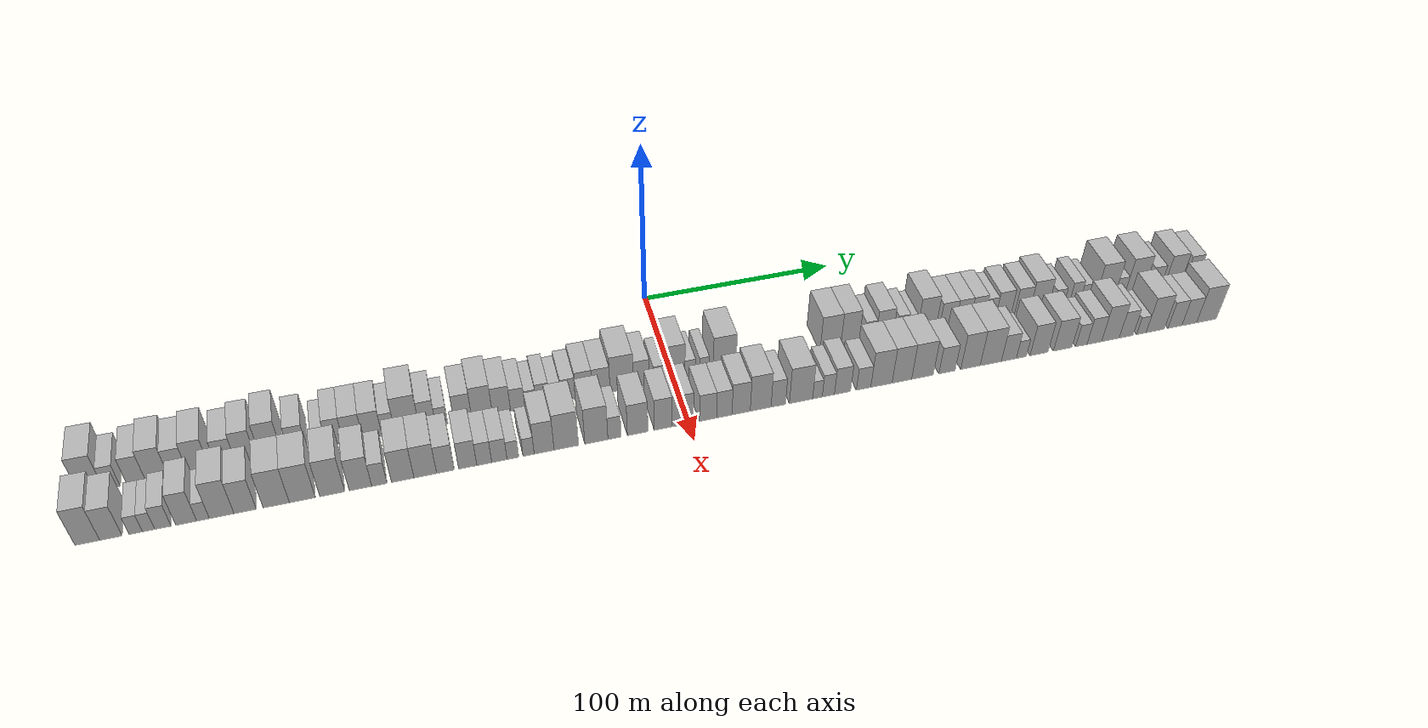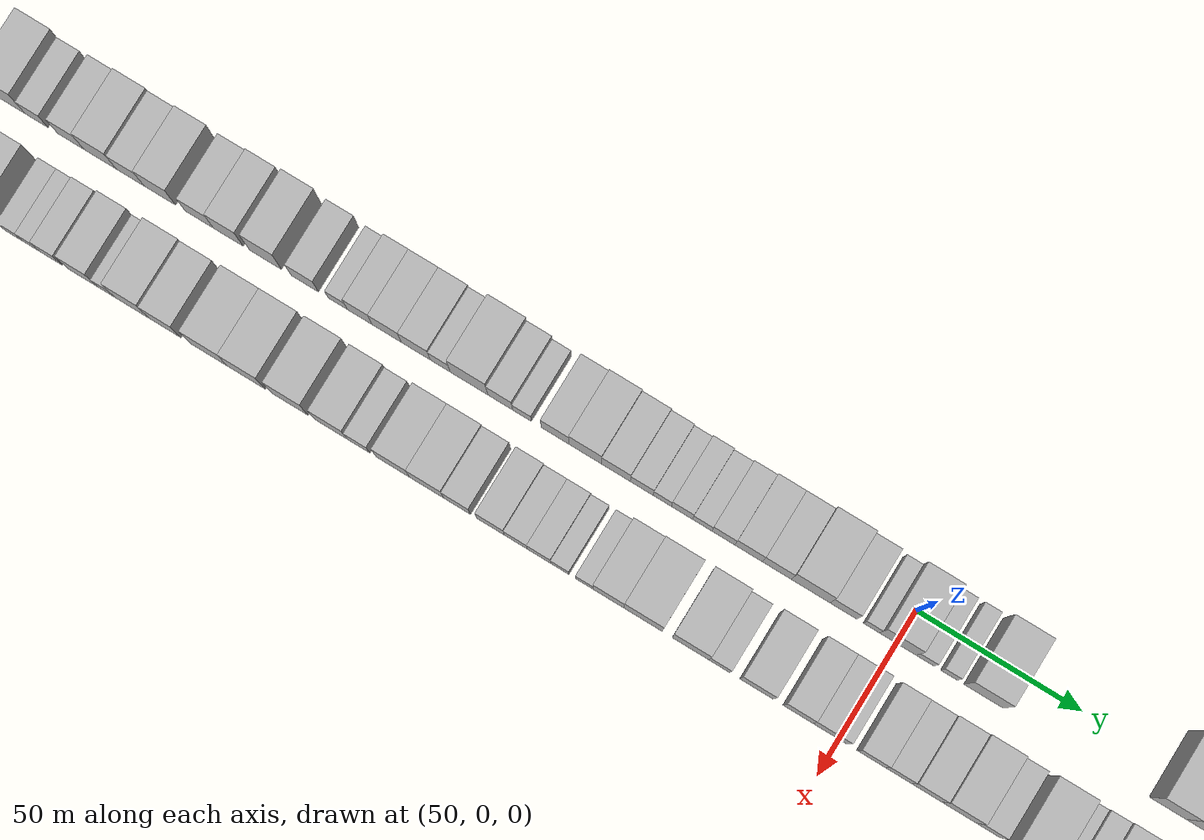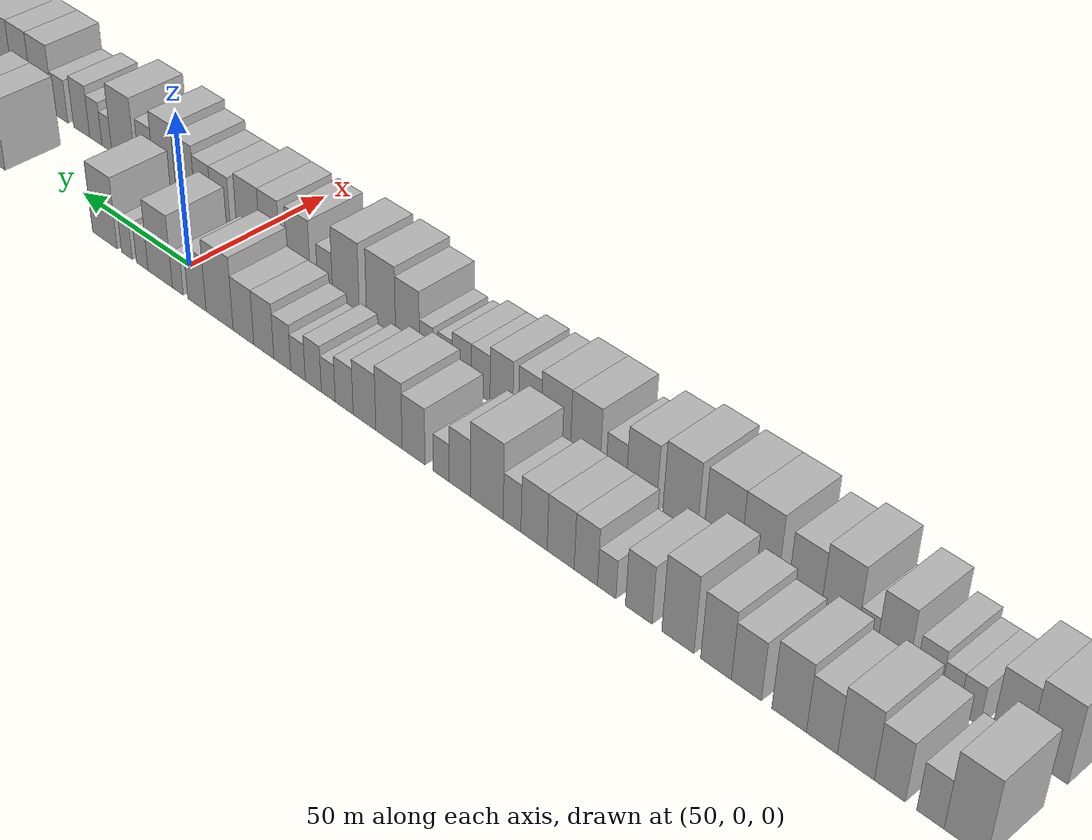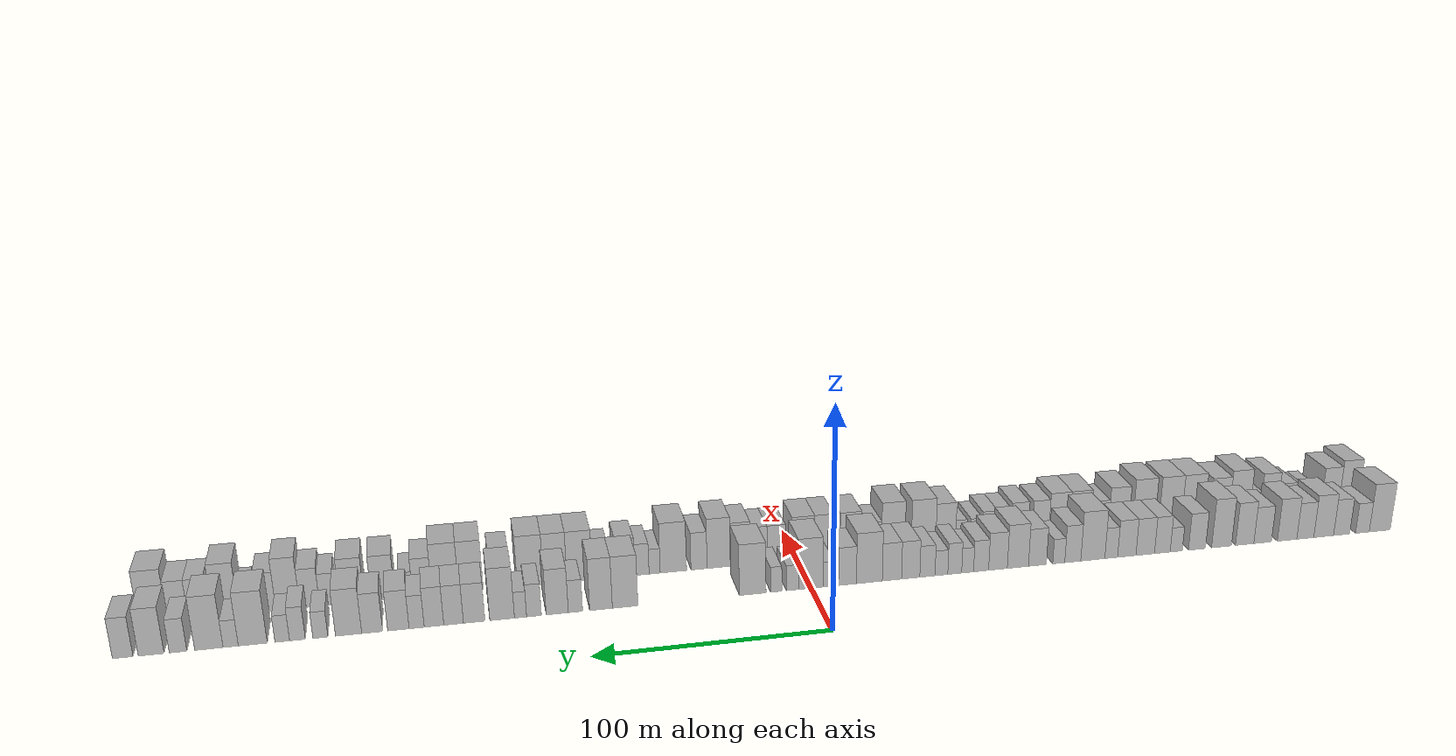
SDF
<sdf version="1.6">
 <world name="default">
  <scene>
   <sky><clouds><speed>12</speed></clouds></sky>
   <ambient>0.4 0.4 0.4 1</ambient>
   <background>0.7 0.7 0.7 1</background>
   <shadows>1</shadows>
  </scene>
  <gravity>0 0 -9.8066</gravity>
  <magnetic_field>6e-06 2.3e-05 -4.2e-05</magnetic_field>
  <physics default="0" name="default_physics" type="ode">
   <ode>
    <solver>
     <type>quick</type>
     <iters>10</iters>
     <sor>1.0</sor>
     <use_dynamic_moi_rescaling>0</use_dynamic_moi_rescaling>
    </solver>
    <constraints>
     <cfm>0</cfm>
     <erp>0.2</erp>
     <contact_max_correcting_vel>100</contact_max_correcting_vel>
     <contact_surface_layer>0.001</contact_surface_layer>
    </constraints>
   </ode>
   <max_step_size>0.004</max_step_size>
   <real_time_factor>1</real_time_factor>
   <real_time_update_rate>250</real_time_update_rate>
  </physics>
  <light name="sun" type="directional">
   <pose>0 0 10 0 0 0</pose>
   <diffuse>0.8 0.8 0.8 1</diffuse>
   <specular>0.2 0.2 0.2 1</specular>
   <attenuation>
    <range>1000</range>
    <constant>0.9</constant>
    <linear>0.01</linear>
    <quadratic>0.001</quadratic>
   </attenuation>
   <direction>-0.5 0.1 -0.9</direction>
  </light>
  <model name="building_1">
   <static>1</static>
   <pose>50.0000 -272.6095 0 0.000000 0.000000 0.000000</pose>
   <link name="link">
    <pose>0 0 12.00 0 0 0</pose>
    <collision name="collision"><geometry><box><size>20.0000 10.7811 24.0000</size></box></geometry></collision>
    <visual name="visual">
     <cast_shadows>0</cast_shadows>
     <geometry><box><size>20.0000 10.7811 24.0000</size></box></geometry>
     <material>
      <script>
       <uri>model://HANNAS_wall/materials/scripts</uri>
       <uri>model://HANNAS_wall/materials/textures</uri>
       <name>vrc/HANNAS_wall</name>
      </script>
     </material>
    </visual>
   </link>
  </model>
  <model name="building_2">
   <static>1</static>
   <pose>50.0000 -263.6989 0 0.000000 0.000000 0.000000</pose>
   <link name="link">
    <pose>0 0 7.50 0 0 0</pose>
    <collision name="collision"><geometry><box><size>20.0000 7.0400 15.0000</size></box></geometry></collision>
    <visual name="visual">
     <cast_shadows>0</cast_shadows>
     <geometry><box><size>20.0000 7.0400 15.0000</size></box></geometry>
     <material>
      <script>
       <uri>model://HANNAS_wall/materials/scripts</uri>
       <uri>model://HANNAS_wall/materials/textures</uri>
       <name>vrc/HANNAS_wall</name>
      </script>
     </material>
    </visual>
   </link>
  </model>
  <model name="building_3">
   <static>1</static>
   <pose>50.0000 -253.0699 0 0.000000 0.000000 0.000000</pose>
   <link name="link">
    <pose>0 0 9.00 0 0 0</pose>
    <collision name="collision"><geometry><box><size>20.0000 8.2181 18.0000</size></box></geometry></collision>
    <visual name="visual">
     <cast_shadows>0</cast_shadows>
     <geometry><box><size>20.0000 8.2181 18.0000</size></box></geometry>
     <material>
      <script>
       <uri>model://HANNAS_wall/materials/scripts</uri>
       <uri>model://HANNAS_wall/materials/textures</uri>
       <name>vrc/HANNAS_wall</name>
      </script>
     </material>
    </visual>
   </link>
  </model>
  <model name="building_4">
   <static>1</static>
   <pose>50.0000 -243.9424 0 0.000000 0.000000 0.000000</pose>
   <link name="link">
    <pose>0 0 10.50 0 0 0</pose>
    <collision name="collision"><geometry><box><size>20.0000 10.0370 21.0000</size></box></geometry></collision>
    <visual name="visual">
     <cast_shadows>0</cast_shadows>
     <geometry><box><size>20.0000 10.0370 21.0000</size></box></geometry>
     <material>
      <script>
       <uri>model://HANNAS_wall/materials/scripts</uri>
       <uri>model://HANNAS_wall/materials/textures</uri>
       <name>vrc/HANNAS_wall</name>
      </script>
     </material>
    </visual>
   </link>
  </model>
  <model name="building_5">
   <static>1</static>
   <pose>50.0000 -234.6155 0 0.000000 0.000000 0.000000</pose>
   <link name="link">
    <pose>0 0 9.00 0 0 0</pose>
    <collision name="collision"><geometry><box><size>20.0000 8.6167 18.0000</size></box></geometry></collision>
    <visual name="visual">
     <cast_shadows>0</cast_shadows>
     <geometry><box><size>20.0000 8.6167 18.0000</size></box></geometry>
     <material>
      <script>
       <uri>model://HANNAS_wall/materials/scripts</uri>
       <uri>model://HANNAS_wall/materials/textures</uri>
       <name>vrc/HANNAS_wall</name>
      </script>
     </material>
    </visual>
   </link>
  </model>
  <model name="building_6">
   <static>1</static>
   <pose>50.0000 -225.4179 0 0.000000 0.000000 0.000000</pose>
   <link name="link">
    <pose>0 0 10.50 0 0 0</pose>
    <collision name="collision"><geometry><box><size>20.0000 9.7786 21.0000</size></box></geometry></collision>
    <visual name="visual">
     <cast_shadows>0</cast_shadows>
     <geometry><box><size>20.0000 9.7786 21.0000</size></box></geometry>
     <material>
      <script>
       <uri>model://HANNAS_wall/materials/scripts</uri>
       <uri>model://HANNAS_wall/materials/textures</uri>
       <name>vrc/HANNAS_wall</name>
      </script>
     </material>
    </visual>
   </link>
  </model>
  <model name="building_7">
   <static>1</static>
   <pose>50.0000 -213.1358 0 0.000000 0.000000 0.000000</pose>
   <link name="link">
    <pose>0 0 9.00 0 0 0</pose>
    <collision name="collision"><geometry><box><size>20.0000 8.7856 18.0000</size></box></geometry></collision>
    <visual name="visual">
     <cast_shadows>0</cast_shadows>
     <geometry><box><size>20.0000 8.7856 18.0000</size></box></geometry>
     <material>
      <script>
       <uri>model://HANNAS_wall/materials/scripts</uri>
       <uri>model://HANNAS_wall/materials/textures</uri>
       <name>vrc/HANNAS_wall</name>
      </script>
     </material>
    </visual>
   </link>
  </model>
  <model name="building_8">
   <static>1</static>
   <pose>50.0000 -204.1743 0 0.000000 0.000000 0.000000</pose>
   <link name="link">
    <pose>0 0 10.50 0 0 0</pose>
    <collision name="collision"><geometry><box><size>20.0000 9.1375 21.0000</size></box></geometry></collision>
    <visual name="visual">
     <cast_shadows>0</cast_shadows>
     <geometry><box><size>20.0000 9.1375 21.0000</size></box></geometry>
     <material>
      <script>
       <uri>model://HANNAS_wall/materials/scripts</uri>
       <uri>model://HANNAS_wall/materials/textures</uri>
       <name>vrc/HANNAS_wall</name>
      </script>
     </material>
    </visual>
   </link>
  </model>
  <model name="building_9">
   <static>1</static>
   <pose>50.0000 -192.6847 0 0.000000 0.000000 0.000000</pose>
   <link name="link">
    <pose>0 0 12.00 0 0 0</pose>
    <collision name="collision"><geometry><box><size>20.0000 9.8418 24.0000</size></box></geometry></collision>
    <visual name="visual">
     <cast_shadows>0</cast_shadows>
     <geometry><box><size>20.0000 9.8418 24.0000</size></box></geometry>
     <material>
      <script>
       <uri>model://HANNAS_wall/materials/scripts</uri>
       <uri>model://HANNAS_wall/materials/textures</uri>
       <name>vrc/HANNAS_wall</name>
      </script>
     </material>
    </visual>
   </link>
  </model>
  <model name="building_10">
   <static>1</static>
   <pose>50.0000 -180.5605 0 0.000000 0.000000 0.000000</pose>
   <link name="link">
    <pose>0 0 9.00 0 0 0</pose>
    <collision name="collision"><geometry><box><size>20.0000 8.4065 18.0000</size></box></geometry></collision>
    <visual name="visual">
     <cast_shadows>0</cast_shadows>
     <geometry><box><size>20.0000 8.4065 18.0000</size></box></geometry>
     <material>
      <script>
       <uri>model://HANNAS_wall/materials/scripts</uri>
       <uri>model://HANNAS_wall/materials/textures</uri>
       <name>vrc/HANNAS_wall</name>
      </script>
     </material>
    </visual>
   </link>
  </model>
  <model name="building_11">
   <static>1</static>
   <pose>50.0000 -170.3896 0 0.000000 0.000000 0.000000</pose>
   <link name="link">
    <pose>0 0 6.00 0 0 0</pose>
    <collision name="collision"><geometry><box><size>20.0000 5.9353 12.0000</size></box></geometry></collision>
    <visual name="visual">
     <cast_shadows>0</cast_shadows>
     <geometry><box><size>20.0000 5.9353 12.0000</size></box></geometry>
     <material>
      <script>
       <uri>model://HANNAS_wall/materials/scripts</uri>
       <uri>model://HANNAS_wall/materials/textures</uri>
       <name>vrc/HANNAS_wall</name>
      </script>
     </material>
    </visual>
   </link>
  </model>
  <model name="building_12">
   <static>1</static>
   <pose>50.0000 -163.6053 0 0.000000 0.000000 0.000000</pose>
   <link name="link">
    <pose>0 0 9.00 0 0 0</pose>
    <collision name="collision"><geometry><box><size>20.0000 7.6333 18.0000</size></box></geometry></collision>
    <visual name="visual">
     <cast_shadows>0</cast_shadows>
     <geometry><box><size>20.0000 7.6333 18.0000</size></box></geometry>
     <material>
      <script>
       <uri>model://HANNAS_wall/materials/scripts</uri>
       <uri>model://HANNAS_wall/materials/textures</uri>
       <name>vrc/HANNAS_wall</name>
      </script>
     </material>
    </visual>
   </link>
  </model>
  <model name="building_13">
   <static>1</static>
   <pose>50.0000 -155.2934 0 0.000000 0.000000 0.000000</pose>
   <link name="link">
    <pose>0 0 9.00 0 0 0</pose>
    <collision name="collision"><geometry><box><size>20.0000 8.9907 18.0000</size></box></geometry></collision>
    <visual name="visual">
     <cast_shadows>0</cast_shadows>
     <geometry><box><size>20.0000 8.9907 18.0000</size></box></geometry>
     <material>
      <script>
       <uri>model://HANNAS_wall/materials/scripts</uri>
       <uri>model://HANNAS_wall/materials/textures</uri>
       <name>vrc/HANNAS_wall</name>
      </script>
     </material>
    </visual>
   </link>
  </model>
  <model name="building_14">
   <static>1</static>
   <pose>50.0000 -146.3652 0 0.000000 0.000000 0.000000</pose>
   <link name="link">
    <pose>0 0 9.00 0 0 0</pose>
    <collision name="collision"><geometry><box><size>20.0000 8.8655 18.0000</size></box></geometry></collision>
    <visual name="visual">
     <cast_shadows>0</cast_shadows>
     <geometry><box><size>20.0000 8.8655 18.0000</size></box></geometry>
     <material>
      <script>
       <uri>model://HANNAS_wall/materials/scripts</uri>
       <uri>model://HANNAS_wall/materials/textures</uri>
       <name>vrc/HANNAS_wall</name>
      </script>
     </material>
    </visual>
   </link>
  </model>
  <model name="building_15">
   <static>1</static>
   <pose>50.0000 -138.8571 0 0.000000 0.000000 0.000000</pose>
   <link name="link">
    <pose>0 0 7.50 0 0 0</pose>
    <collision name="collision"><geometry><box><size>20.0000 6.1508 15.0000</size></box></geometry></collision>
    <visual name="visual">
     <cast_shadows>0</cast_shadows>
     <geometry><box><size>20.0000 6.1508 15.0000</size></box></geometry>
     <material>
      <script>
       <uri>model://HANNAS_wall/materials/scripts</uri>
       <uri>model://HANNAS_wall/materials/textures</uri>
       <name>vrc/HANNAS_wall</name>
      </script>
     </material>
    </visual>
   </link>
  </model>
  <model name="building_16">
   <static>1</static>
   <pose>50.0000 -130.0185 0 0.000000 0.000000 0.000000</pose>
   <link name="link">
    <pose>0 0 12.00 0 0 0</pose>
    <collision name="collision"><geometry><box><size>20.0000 11.5264 24.0000</size></box></geometry></collision>
    <visual name="visual">
     <cast_shadows>0</cast_shadows>
     <geometry><box><size>20.0000 11.5264 24.0000</size></box></geometry>
     <material>
      <script>
       <uri>model://HANNAS_wall/materials/scripts</uri>
       <uri>model://HANNAS_wall/materials/textures</uri>
       <name>vrc/HANNAS_wall</name>
      </script>
     </material>
    </visual>
   </link>
  </model>
  <model name="building_17">
   <static>1</static>
   <pose>50.0000 -120.4466 0 0.000000 0.000000 0.000000</pose>
   <link name="link">
    <pose>0 0 9.00 0 0 0</pose>
    <collision name="collision"><geometry><box><size>20.0000 7.6174 18.0000</size></box></geometry></collision>
    <visual name="visual">
     <cast_shadows>0</cast_shadows>
     <geometry><box><size>20.0000 7.6174 18.0000</size></box></geometry>
     <material>
      <script>
       <uri>model://HANNAS_wall/materials/scripts</uri>
       <uri>model://HANNAS_wall/materials/textures</uri>
       <name>vrc/HANNAS_wall</name>
      </script>
     </material>
    </visual>
   </link>
  </model>
  <model name="building_18">
   <static>1</static>
   <pose>50.0000 -113.7780 0 0.000000 0.000000 0.000000</pose>
   <link name="link">
    <pose>0 0 6.00 0 0 0</pose>
    <collision name="collision"><geometry><box><size>20.0000 5.7198 12.0000</size></box></geometry></collision>
    <visual name="visual">
     <cast_shadows>0</cast_shadows>
     <geometry><box><size>20.0000 5.7198 12.0000</size></box></geometry>
     <material>
      <script>
       <uri>model://HANNAS_wall/materials/scripts</uri>
       <uri>model://HANNAS_wall/materials/textures</uri>
       <name>vrc/HANNAS_wall</name>
      </script>
     </material>
    </visual>
   </link>
  </model>
  <model name="building_19">
   <static>1</static>
   <pose>50.0000 -103.6759 0 0.000000 0.000000 0.000000</pose>
   <link name="link">
    <pose>0 0 9.00 0 0 0</pose>
    <collision name="collision"><geometry><box><size>20.0000 8.4845 18.0000</size></box></geometry></collision>
    <visual name="visual">
     <cast_shadows>0</cast_shadows>
     <geometry><box><size>20.0000 8.4845 18.0000</size></box></geometry>
     <material>
      <script>
       <uri>model://HANNAS_wall/materials/scripts</uri>
       <uri>model://HANNAS_wall/materials/textures</uri>
       <name>vrc/HANNAS_wall</name>
      </script>
     </material>
    </visual>
   </link>
  </model>
  <model name="building_20">
   <static>1</static>
   <pose>50.0000 -94.4692 0 0.000000 0.000000 0.000000</pose>
   <link name="link">
    <pose>0 0 10.50 0 0 0</pose>
    <collision name="collision"><geometry><box><size>20.0000 9.9289 21.0000</size></box></geometry></collision>
    <visual name="visual">
     <cast_shadows>0</cast_shadows>
     <geometry><box><size>20.0000 9.9289 21.0000</size></box></geometry>
     <material>
      <script>
       <uri>model://HANNAS_wall/materials/scripts</uri>
       <uri>model://HANNAS_wall/materials/textures</uri>
       <name>vrc/HANNAS_wall</name>
      </script>
     </material>
    </visual>
   </link>
  </model>
  <model name="building_21">
   <static>1</static>
   <pose>50.0000 -85.1361 0 0.000000 0.000000 0.000000</pose>
   <link name="link">
    <pose>0 0 9.00 0 0 0</pose>
    <collision name="collision"><geometry><box><size>20.0000 8.7373 18.0000</size></box></geometry></collision>
    <visual name="visual">
     <cast_shadows>0</cast_shadows>
     <geometry><box><size>20.0000 8.7373 18.0000</size></box></geometry>
     <material>
      <script>
       <uri>model://HANNAS_wall/materials/scripts</uri>
       <uri>model://HANNAS_wall/materials/textures</uri>
       <name>vrc/HANNAS_wall</name>
      </script>
     </material>
    </visual>
   </link>
  </model>
  <model name="building_22">
   <static>1</static>
   <pose>50.0000 -77.2666 0 0.000000 0.000000 0.000000</pose>
   <link name="link">
    <pose>0 0 7.50 0 0 0</pose>
    <collision name="collision"><geometry><box><size>20.0000 7.0017 15.0000</size></box></geometry></collision>
    <visual name="visual">
     <cast_shadows>0</cast_shadows>
     <geometry><box><size>20.0000 7.0017 15.0000</size></box></geometry>
     <material>
      <script>
       <uri>model://HANNAS_wall/materials/scripts</uri>
       <uri>model://HANNAS_wall/materials/textures</uri>
       <name>vrc/HANNAS_wall</name>
      </script>
     </material>
    </visual>
   </link>
  </model>
  <model name="building_23">
   <static>1</static>
   <pose>50.0000 -71.0025 0 0.000000 0.000000 0.000000</pose>
   <link name="link">
    <pose>0 0 6.00 0 0 0</pose>
    <collision name="collision"><geometry><box><size>20.0000 5.5265 12.0000</size></box></geometry></collision>
    <visual name="visual">
     <cast_shadows>0</cast_shadows>
     <geometry><box><size>20.0000 5.5265 12.0000</size></box></geometry>
     <material>
      <script>
       <uri>model://HANNAS_wall/materials/scripts</uri>
       <uri>model://HANNAS_wall/materials/textures</uri>
       <name>vrc/HANNAS_wall</name>
      </script>
     </material>
    </visual>
   </link>
  </model>
  <model name="building_24">
   <static>1</static>
   <pose>50.0000 -65.0267 0 0.000000 0.000000 0.000000</pose>
   <link name="link">
    <pose>0 0 7.50 0 0 0</pose>
    <collision name="collision"><geometry><box><size>20.0000 6.4250 15.0000</size></box></geometry></collision>
    <visual name="visual">
     <cast_shadows>0</cast_shadows>
     <geometry><box><size>20.0000 6.4250 15.0000</size></box></geometry>
     <material>
      <script>
       <uri>model://HANNAS_wall/materials/scripts</uri>
       <uri>model://HANNAS_wall/materials/textures</uri>
       <name>vrc/HANNAS_wall</name>
      </script>
     </material>
    </visual>
   </link>
  </model>
  <model name="building_25">
   <static>1</static>
   <pose>50.0000 -58.8759 0 0.000000 0.000000 0.000000</pose>
   <link name="link">
    <pose>0 0 6.00 0 0 0</pose>
    <collision name="collision"><geometry><box><size>20.0000 5.8766 12.0000</size></box></geometry></collision>
    <visual name="visual">
     <cast_shadows>0</cast_shadows>
     <geometry><box><size>20.0000 5.8766 12.0000</size></box></geometry>
     <material>
      <script>
       <uri>model://HANNAS_wall/materials/scripts</uri>
       <uri>model://HANNAS_wall/materials/textures</uri>
       <name>vrc/HANNAS_wall</name>
      </script>
     </material>
    </visual>
   </link>
  </model>
  <model name="building_26">
   <static>1</static>
   <pose>50.0000 -52.4413 0 0.000000 0.000000 0.000000</pose>
   <link name="link">
    <pose>0 0 7.50 0 0 0</pose>
    <collision name="collision"><geometry><box><size>20.0000 6.9926 15.0000</size></box></geometry></collision>
    <visual name="visual">
     <cast_shadows>0</cast_shadows>
     <geometry><box><size>20.0000 6.9926 15.0000</size></box></geometry>
     <material>
      <script>
       <uri>model://HANNAS_wall/materials/scripts</uri>
       <uri>model://HANNAS_wall/materials/textures</uri>
       <name>vrc/HANNAS_wall</name>
      </script>
     </material>
    </visual>
   </link>
  </model>
  <model name="building_27">
   <static>1</static>
   <pose>50.0000 -44.7642 0 0.000000 0.000000 0.000000</pose>
   <link name="link">
    <pose>0 0 9.00 0 0 0</pose>
    <collision name="collision"><geometry><box><size>20.0000 8.3615 18.0000</size></box></geometry></collision>
    <visual name="visual">
     <cast_shadows>0</cast_shadows>
     <geometry><box><size>20.0000 8.3615 18.0000</size></box></geometry>
     <material>
      <script>
       <uri>model://HANNAS_wall/materials/scripts</uri>
       <uri>model://HANNAS_wall/materials/textures</uri>
       <name>vrc/HANNAS_wall</name>
      </script>
     </material>
    </visual>
   </link>
  </model>
  <model name="building_28">
   <static>1</static>
   <pose>50.0000 -36.2077 0 0.000000 0.000000 0.000000</pose>
   <link name="link">
    <pose>0 0 9.00 0 0 0</pose>
    <collision name="collision"><geometry><box><size>20.0000 8.7515 18.0000</size></box></geometry></collision>
    <visual name="visual">
     <cast_shadows>0</cast_shadows>
     <geometry><box><size>20.0000 8.7515 18.0000</size></box></geometry>
     <material>
      <script>
       <uri>model://HANNAS_wall/materials/scripts</uri>
       <uri>model://HANNAS_wall/materials/textures</uri>
       <name>vrc/HANNAS_wall</name>
      </script>
     </material>
    </visual>
   </link>
  </model>
  <model name="building_29">
   <static>1</static>
   <pose>50.0000 -25.9818 0 0.000000 0.000000 0.000000</pose>
   <link name="link">
    <pose>0 0 12.00 0 0 0</pose>
    <collision name="collision"><geometry><box><size>20.0000 11.7005 24.0000</size></box></geometry></collision>
    <visual name="visual">
     <cast_shadows>0</cast_shadows>
     <geometry><box><size>20.0000 11.7005 24.0000</size></box></geometry>
     <material>
      <script>
       <uri>model://HANNAS_wall/materials/scripts</uri>
       <uri>model://HANNAS_wall/materials/textures</uri>
       <name>vrc/HANNAS_wall</name>
      </script>
     </material>
    </visual>
   </link>
  </model>
  <model name="building_30">
   <static>1</static>
   <pose>50.0000 -16.0936 0 0.000000 0.000000 0.000000</pose>
   <link name="link">
    <pose>0 0 9.00 0 0 0</pose>
    <collision name="collision"><geometry><box><size>20.0000 8.0759 18.0000</size></box></geometry></collision>
    <visual name="visual">
     <cast_shadows>0</cast_shadows>
     <geometry><box><size>20.0000 8.0759 18.0000</size></box></geometry>
     <material>
      <script>
       <uri>model://HANNAS_wall/materials/scripts</uri>
       <uri>model://HANNAS_wall/materials/textures</uri>
       <name>vrc/HANNAS_wall</name>
      </script>
     </material>
    </visual>
   </link>
  </model>
  <model name="building_31">
   <static>1</static>
   <pose>50.0000 -7.6204 0 0.000000 0.000000 0.000000</pose>
   <link name="link">
    <pose>0 0 6.00 0 0 0</pose>
    <collision name="collision"><geometry><box><size>20.0000 4.8705 12.0000</size></box></geometry></collision>
    <visual name="visual">
     <cast_shadows>0</cast_shadows>
     <geometry><box><size>20.0000 4.8705 12.0000</size></box></geometry>
     <material>
      <script>
       <uri>model://HANNAS_wall/materials/scripts</uri>
       <uri>model://HANNAS_wall/materials/textures</uri>
       <name>vrc/HANNAS_wall</name>
      </script>
     </material>
    </visual>
   </link>
  </model>
  <model name="building_32">
   <static>1</static>
   <pose>50.0000 0.3281 0 0.000000 0.000000 0.000000</pose>
   <link name="link">
    <pose>0 0 12.00 0 0 0</pose>
    <collision name="collision"><geometry><box><size>20.0000 11.0267 24.0000</size></box></geometry></collision>
    <visual name="visual">
     <cast_shadows>0</cast_shadows>
     <geometry><box><size>20.0000 11.0267 24.0000</size></box></geometry>
     <material>
      <script>
       <uri>model://HANNAS_wall/materials/scripts</uri>
       <uri>model://HANNAS_wall/materials/textures</uri>
       <name>vrc/HANNAS_wall</name>
      </script>
     </material>
    </visual>
   </link>
  </model>
  <model name="building_33">
   <static>1</static>
   <pose>50.0000 8.5430 0 0.000000 0.000000 0.000000</pose>
   <link name="link">
    <pose>0 0 6.00 0 0 0</pose>
    <collision name="collision"><geometry><box><size>20.0000 5.4030 12.0000</size></box></geometry></collision>
    <visual name="visual">
     <cast_shadows>0</cast_shadows>
     <geometry><box><size>20.0000 5.4030 12.0000</size></box></geometry>
     <material>
      <script>
       <uri>model://HANNAS_wall/materials/scripts</uri>
       <uri>model://HANNAS_wall/materials/textures</uri>
       <name>vrc/HANNAS_wall</name>
      </script>
     </material>
    </visual>
   </link>
  </model>
  <model name="building_34">
   <static>1</static>
   <pose>50.0000 15.7394 0 0.000000 0.000000 0.000000</pose>
   <link name="link">
    <pose>0 0 6.00 0 0 0</pose>
    <collision name="collision"><geometry><box><size>20.0000 4.9897 12.0000</size></box></geometry></collision>
    <visual name="visual">
     <cast_shadows>0</cast_shadows>
     <geometry><box><size>20.0000 4.9897 12.0000</size></box></geometry>
     <material>
      <script>
       <uri>model://HANNAS_wall/materials/scripts</uri>
       <uri>model://HANNAS_wall/materials/textures</uri>
       <name>vrc/HANNAS_wall</name>
      </script>
     </material>
    </visual>
   </link>
  </model>
  <model name="building_35">
   <static>1</static>
   <pose>50.0000 26.1092 0 0.000000 0.000000 0.000000</pose>
   <link name="link">
    <pose>0 0 12.00 0 0 0</pose>
    <collision name="collision"><geometry><box><size>20.0000 11.7500 24.0000</size></box></geometry></collision>
    <visual name="visual">
     <cast_shadows>0</cast_shadows>
     <geometry><box><size>20.0000 11.7500 24.0000</size></box></geometry>
     <material>
      <script>
       <uri>model://HANNAS_wall/materials/scripts</uri>
       <uri>model://HANNAS_wall/materials/textures</uri>
       <name>vrc/HANNAS_wall</name>
      </script>
     </material>
    </visual>
   </link>
  </model>
  <model name="building_36">
   <static>1</static>
   <pose>50.0000 81.3536 0 0.000000 0.000000 0.000000</pose>
   <link name="link">
    <pose>0 0 12.00 0 0 0</pose>
    <collision name="collision"><geometry><box><size>20.0000 10.9129 24.0000</size></box></geometry></collision>
    <visual name="visual">
     <cast_shadows>0</cast_shadows>
     <geometry><box><size>20.0000 10.9129 24.0000</size></box></geometry>
     <material>
      <script>
       <uri>model://HANNAS_wall/materials/scripts</uri>
       <uri>model://HANNAS_wall/materials/textures</uri>
       <name>vrc/HANNAS_wall</name>
      </script>
     </material>
    </visual>
   </link>
  </model>
  <model name="building_37">
   <static>1</static>
   <pose>50.0000 91.6201 0 0.000000 0.000000 0.000000</pose>
   <link name="link">
    <pose>0 0 12.00 0 0 0</pose>
    <collision name="collision"><geometry><box><size>20.0000 9.6200 24.0000</size></box></geometry></collision>
    <visual name="visual">
     <cast_shadows>0</cast_shadows>
     <geometry><box><size>20.0000 9.6200 24.0000</size></box></geometry>
     <material>
      <script>
       <uri>model://HANNAS_wall/materials/scripts</uri>
       <uri>model://HANNAS_wall/materials/textures</uri>
       <name>vrc/HANNAS_wall</name>
      </script>
     </material>
    </visual>
   </link>
  </model>
  <model name="building_38">
   <static>1</static>
   <pose>50.0000 102.4375 0 0.000000 0.000000 0.000000</pose>
   <link name="link">
    <pose>0 0 7.50 0 0 0</pose>
    <collision name="collision"><geometry><box><size>20.0000 6.0148 15.0000</size></box></geometry></collision>
    <visual name="visual">
     <cast_shadows>0</cast_shadows>
     <geometry><box><size>20.0000 6.0148 15.0000</size></box></geometry>
     <material>
      <script>
       <uri>model://HANNAS_wall/materials/scripts</uri>
       <uri>model://HANNAS_wall/materials/textures</uri>
       <name>vrc/HANNAS_wall</name>
      </script>
     </material>
    </visual>
   </link>
  </model>
  <model name="building_39">
   <static>1</static>
   <pose>50.0000 110.0867 0 0.000000 0.000000 0.000000</pose>
   <link name="link">
    <pose>0 0 10.50 0 0 0</pose>
    <collision name="collision"><geometry><box><size>20.0000 9.2836 21.0000</size></box></geometry></collision>
    <visual name="visual">
     <cast_shadows>0</cast_shadows>
     <geometry><box><size>20.0000 9.2836 21.0000</size></box></geometry>
     <material>
      <script>
       <uri>model://HANNAS_wall/materials/scripts</uri>
       <uri>model://HANNAS_wall/materials/textures</uri>
       <name>vrc/HANNAS_wall</name>
      </script>
     </material>
    </visual>
   </link>
  </model>
  <model name="building_40">
   <static>1</static>
   <pose>50.0000 119.8254 0 0.000000 0.000000 0.000000</pose>
   <link name="link">
    <pose>0 0 7.50 0 0 0</pose>
    <collision name="collision"><geometry><box><size>20.0000 6.1937 15.0000</size></box></geometry></collision>
    <visual name="visual">
     <cast_shadows>0</cast_shadows>
     <geometry><box><size>20.0000 6.1937 15.0000</size></box></geometry>
     <material>
      <script>
       <uri>model://HANNAS_wall/materials/scripts</uri>
       <uri>model://HANNAS_wall/materials/textures</uri>
       <name>vrc/HANNAS_wall</name>
      </script>
     </material>
    </visual>
   </link>
  </model>
  <model name="building_41">
   <static>1</static>
   <pose>50.0000 125.4484 0 0.000000 0.000000 0.000000</pose>
   <link name="link">
    <pose>0 0 6.00 0 0 0</pose>
    <collision name="collision"><geometry><box><size>20.0000 5.0524 12.0000</size></box></geometry></collision>
    <visual name="visual">
     <cast_shadows>0</cast_shadows>
     <geometry><box><size>20.0000 5.0524 12.0000</size></box></geometry>
     <material>
      <script>
       <uri>model://HANNAS_wall/materials/scripts</uri>
       <uri>model://HANNAS_wall/materials/textures</uri>
       <name>vrc/HANNAS_wall</name>
      </script>
     </material>
    </visual>
   </link>
  </model>
  <model name="building_42">
   <static>1</static>
   <pose>50.0000 133.0787 0 0.000000 0.000000 0.000000</pose>
   <link name="link">
    <pose>0 0 12.00 0 0 0</pose>
    <collision name="collision"><geometry><box><size>20.0000 10.2081 24.0000</size></box></geometry></collision>
    <visual name="visual">
     <cast_shadows>0</cast_shadows>
     <geometry><box><size>20.0000 10.2081 24.0000</size></box></geometry>
     <material>
      <script>
       <uri>model://HANNAS_wall/materials/scripts</uri>
       <uri>model://HANNAS_wall/materials/textures</uri>
       <name>vrc/HANNAS_wall</name>
      </script>
     </material>
    </visual>
   </link>
  </model>
  <model name="building_43">
   <static>1</static>
   <pose>50.0000 144.6121 0 0.000000 0.000000 0.000000</pose>
   <link name="link">
    <pose>0 0 9.00 0 0 0</pose>
    <collision name="collision"><geometry><box><size>20.0000 8.8586 18.0000</size></box></geometry></collision>
    <visual name="visual">
     <cast_shadows>0</cast_shadows>
     <geometry><box><size>20.0000 8.8586 18.0000</size></box></geometry>
     <material>
      <script>
       <uri>model://HANNAS_wall/materials/scripts</uri>
       <uri>model://HANNAS_wall/materials/textures</uri>
       <name>vrc/HANNAS_wall</name>
      </script>
     </material>
    </visual>
   </link>
  </model>
  <model name="building_44">
   <static>1</static>
   <pose>50.0000 153.0716 0 0.000000 0.000000 0.000000</pose>
   <link name="link">
    <pose>0 0 9.00 0 0 0</pose>
    <collision name="collision"><geometry><box><size>20.0000 8.0604 18.0000</size></box></geometry></collision>
    <visual name="visual">
     <cast_shadows>0</cast_shadows>
     <geometry><box><size>20.0000 8.0604 18.0000</size></box></geometry>
     <material>
      <script>
       <uri>model://HANNAS_wall/materials/scripts</uri>
       <uri>model://HANNAS_wall/materials/textures</uri>
       <name>vrc/HANNAS_wall</name>
      </script>
     </material>
    </visual>
   </link>
  </model>
  <model name="building_45">
   <static>1</static>
   <pose>50.0000 161.0884 0 0.000000 0.000000 0.000000</pose>
   <link name="link">
    <pose>0 0 9.00 0 0 0</pose>
    <collision name="collision"><geometry><box><size>20.0000 7.9732 18.0000</size></box></geometry></collision>
    <visual name="visual">
     <cast_shadows>0</cast_shadows>
     <geometry><box><size>20.0000 7.9732 18.0000</size></box></geometry>
     <material>
      <script>
       <uri>model://HANNAS_wall/materials/scripts</uri>
       <uri>model://HANNAS_wall/materials/textures</uri>
       <name>vrc/HANNAS_wall</name>
      </script>
     </material>
    </visual>
   </link>
  </model>
  <model name="building_46">
   <static>1</static>
   <pose>50.0000 168.1415 0 0.000000 0.000000 0.000000</pose>
   <link name="link">
    <pose>0 0 7.50 0 0 0</pose>
    <collision name="collision"><geometry><box><size>20.0000 6.1328 15.0000</size></box></geometry></collision>
    <visual name="visual">
     <cast_shadows>0</cast_shadows>
     <geometry><box><size>20.0000 6.1328 15.0000</size></box></geometry>
     <material>
      <script>
       <uri>model://HANNAS_wall/materials/scripts</uri>
       <uri>model://HANNAS_wall/materials/textures</uri>
       <name>vrc/HANNAS_wall</name>
      </script>
     </material>
    </visual>
   </link>
  </model>
  <model name="building_47">
   <static>1</static>
   <pose>50.0000 175.5338 0 0.000000 0.000000 0.000000</pose>
   <link name="link">
    <pose>0 0 9.00 0 0 0</pose>
    <collision name="collision"><geometry><box><size>20.0000 8.6520 18.0000</size></box></geometry></collision>
    <visual name="visual">
     <cast_shadows>0</cast_shadows>
     <geometry><box><size>20.0000 8.6520 18.0000</size></box></geometry>
     <material>
      <script>
       <uri>model://HANNAS_wall/materials/scripts</uri>
       <uri>model://HANNAS_wall/materials/textures</uri>
       <name>vrc/HANNAS_wall</name>
      </script>
     </material>
    </visual>
   </link>
  </model>
  <model name="building_48">
   <static>1</static>
   <pose>50.0000 186.0772 0 0.000000 0.000000 0.000000</pose>
   <link name="link">
    <pose>0 0 9.00 0 0 0</pose>
    <collision name="collision"><geometry><box><size>20.0000 8.4348 18.0000</size></box></geometry></collision>
    <visual name="visual">
     <cast_shadows>0</cast_shadows>
     <geometry><box><size>20.0000 8.4348 18.0000</size></box></geometry>
     <material>
      <script>
       <uri>model://HANNAS_wall/materials/scripts</uri>
       <uri>model://HANNAS_wall/materials/textures</uri>
       <name>vrc/HANNAS_wall</name>
      </script>
     </material>
    </visual>
   </link>
  </model>
  <model name="building_49">
   <static>1</static>
   <pose>50.0000 195.5442 0 0.000000 0.000000 0.000000</pose>
   <link name="link">
    <pose>0 0 10.50 0 0 0</pose>
    <collision name="collision"><geometry><box><size>20.0000 10.4991 21.0000</size></box></geometry></collision>
    <visual name="visual">
     <cast_shadows>0</cast_shadows>
     <geometry><box><size>20.0000 10.4991 21.0000</size></box></geometry>
     <material>
      <script>
       <uri>model://HANNAS_wall/materials/scripts</uri>
       <uri>model://HANNAS_wall/materials/textures</uri>
       <name>vrc/HANNAS_wall</name>
      </script>
     </material>
    </visual>
   </link>
  </model>
  <model name="building_50">
   <static>1</static>
   <pose>50.0000 206.7703 0 0.000000 0.000000 0.000000</pose>
   <link name="link">
    <pose>0 0 6.00 0 0 0</pose>
    <collision name="collision"><geometry><box><size>20.0000 5.9532 12.0000</size></box></geometry></collision>
    <visual name="visual">
     <cast_shadows>0</cast_shadows>
     <geometry><box><size>20.0000 5.9532 12.0000</size></box></geometry>
     <material>
      <script>
       <uri>model://HANNAS_wall/materials/scripts</uri>
       <uri>model://HANNAS_wall/materials/textures</uri>
       <name>vrc/HANNAS_wall</name>
      </script>
     </material>
    </visual>
   </link>
  </model>
  <model name="building_51">
   <static>1</static>
   <pose>50.0000 215.8573 0 0.000000 0.000000 0.000000</pose>
   <link name="link">
    <pose>0 0 7.50 0 0 0</pose>
    <collision name="collision"><geometry><box><size>20.0000 6.2208 15.0000</size></box></geometry></collision>
    <visual name="visual">
     <cast_shadows>0</cast_shadows>
     <geometry><box><size>20.0000 6.2208 15.0000</size></box></geometry>
     <material>
      <script>
       <uri>model://HANNAS_wall/materials/scripts</uri>
       <uri>model://HANNAS_wall/materials/textures</uri>
       <name>vrc/HANNAS_wall</name>
      </script>
     </material>
    </visual>
   </link>
  </model>
  <model name="building_52">
   <static>1</static>
   <pose>50.0000 221.8595 0 0.000000 0.000000 0.000000</pose>
   <link name="link">
    <pose>0 0 6.00 0 0 0</pose>
    <collision name="collision"><geometry><box><size>20.0000 5.7837 12.0000</size></box></geometry></collision>
    <visual name="visual">
     <cast_shadows>0</cast_shadows>
     <geometry><box><size>20.0000 5.7837 12.0000</size></box></geometry>
     <material>
      <script>
       <uri>model://HANNAS_wall/materials/scripts</uri>
       <uri>model://HANNAS_wall/materials/textures</uri>
       <name>vrc/HANNAS_wall</name>
      </script>
     </material>
    </visual>
   </link>
  </model>
  <model name="building_53">
   <static>1</static>
   <pose>50.0000 233.4132 0 0.000000 0.000000 0.000000</pose>
   <link name="link">
    <pose>0 0 12.00 0 0 0</pose>
    <collision name="collision"><geometry><box><size>20.0000 11.3236 24.0000</size></box></geometry></collision>
    <visual name="visual">
     <cast_shadows>0</cast_shadows>
     <geometry><box><size>20.0000 11.3236 24.0000</size></box></geometry>
     <material>
      <script>
       <uri>model://HANNAS_wall/materials/scripts</uri>
       <uri>model://HANNAS_wall/materials/textures</uri>
       <name>vrc/HANNAS_wall</name>
      </script>
     </material>
    </visual>
   </link>
  </model>
  <model name="building_54">
   <static>1</static>
   <pose>50.0000 242.0458 0 0.000000 0.000000 0.000000</pose>
   <link name="link">
    <pose>0 0 6.00 0 0 0</pose>
    <collision name="collision"><geometry><box><size>20.0000 5.9414 12.0000</size></box></geometry></collision>
    <visual name="visual">
     <cast_shadows>0</cast_shadows>
     <geometry><box><size>20.0000 5.9414 12.0000</size></box></geometry>
     <material>
      <script>
       <uri>model://HANNAS_wall/materials/scripts</uri>
       <uri>model://HANNAS_wall/materials/textures</uri>
       <name>vrc/HANNAS_wall</name>
      </script>
     </material>
    </visual>
   </link>
  </model>
  <model name="building_55">
   <static>1</static>
   <pose>50.0000 250.5030 0 0.000000 0.000000 0.000000</pose>
   <link name="link">
    <pose>0 0 12.00 0 0 0</pose>
    <collision name="collision"><geometry><box><size>20.0000 10.9730 24.0000</size></box></geometry></collision>
    <visual name="visual">
     <cast_shadows>0</cast_shadows>
     <geometry><box><size>20.0000 10.9730 24.0000</size></box></geometry>
     <material>
      <script>
       <uri>model://HANNAS_wall/materials/scripts</uri>
       <uri>model://HANNAS_wall/materials/textures</uri>
       <name>vrc/HANNAS_wall</name>
      </script>
     </material>
    </visual>
   </link>
  </model>
  <model name="building_56">
   <static>1</static>
   <pose>50.0000 262.3821 0 0.000000 0.000000 0.000000</pose>
   <link name="link">
    <pose>0 0 7.50 0 0 0</pose>
    <collision name="collision"><geometry><box><size>20.0000 6.7853 15.0000</size></box></geometry></collision>
    <visual name="visual">
     <cast_shadows>0</cast_shadows>
     <geometry><box><size>20.0000 6.7853 15.0000</size></box></geometry>
     <material>
      <script>
       <uri>model://HANNAS_wall/materials/scripts</uri>
       <uri>model://HANNAS_wall/materials/textures</uri>
       <name>vrc/HANNAS_wall</name>
      </script>
     </material>
    </visual>
   </link>
  </model>
  <model name="building_57">
   <static>1</static>
   <pose>50.0000 272.6930 0 0.000000 0.000000 0.000000</pose>
   <link name="link">
    <pose>0 0 10.50 0 0 0</pose>
    <collision name="collision"><geometry><box><size>20.0000 9.8365 21.0000</size></box></geometry></collision>
    <visual name="visual">
     <cast_shadows>0</cast_shadows>
     <geometry><box><size>20.0000 9.8365 21.0000</size></box></geometry>
     <material>
      <script>
       <uri>model://HANNAS_wall/materials/scripts</uri>
       <uri>model://HANNAS_wall/materials/textures</uri>
       <name>vrc/HANNAS_wall</name>
      </script>
     </material>
    </visual>
   </link>
  </model>
  <model name="building_58">
   <static>1</static>
   <pose>50.0000 283.5262 0 0.000000 0.000000 0.000000</pose>
   <link name="link">
    <pose>0 0 9.00 0 0 0</pose>
    <collision name="collision"><geometry><box><size>20.0000 7.8297 18.0000</size></box></geometry></collision>
    <visual name="visual">
     <cast_shadows>0</cast_shadows>
     <geometry><box><size>20.0000 7.8297 18.0000</size></box></geometry>
     <material>
      <script>
       <uri>model://HANNAS_wall/materials/scripts</uri>
       <uri>model://HANNAS_wall/materials/textures</uri>
       <name>vrc/HANNAS_wall</name>
      </script>
     </material>
    </visual>
   </link>
  </model>
  <model name="building_59">
   <static>1</static>
   <pose>79.0000 -272.8088 0 0.000000 0.000000 0.000000</pose>
   <link name="link">
    <pose>0 0 12.00 0 0 0</pose>
    <collision name="collision"><geometry><box><size>20.0000 10.3825 24.0000</size></box></geometry></collision>
    <visual name="visual">
     <cast_shadows>0</cast_shadows>
     <geometry><box><size>20.0000 10.3825 24.0000</size></box></geometry>
     <material>
      <script>
       <uri>model://HANNAS_wall/materials/scripts</uri>
       <uri>model://HANNAS_wall/materials/textures</uri>
       <name>vrc/HANNAS_wall</name>
      </script>
     </material>
    </visual>
   </link>
  </model>
  <model name="building_60">
   <static>1</static>
   <pose>79.0000 -262.9239 0 0.000000 0.000000 0.000000</pose>
   <link name="link">
    <pose>0 0 10.50 0 0 0</pose>
    <collision name="collision"><geometry><box><size>20.0000 9.3872 21.0000</size></box></geometry></collision>
    <visual name="visual">
     <cast_shadows>0</cast_shadows>
     <geometry><box><size>20.0000 9.3872 21.0000</size></box></geometry>
     <material>
      <script>
       <uri>model://HANNAS_wall/materials/scripts</uri>
       <uri>model://HANNAS_wall/materials/textures</uri>
       <name>vrc/HANNAS_wall</name>
      </script>
     </material>
    </visual>
   </link>
  </model>
  <model name="building_61">
   <static>1</static>
   <pose>79.0000 -252.4113 0 0.000000 0.000000 0.000000</pose>
   <link name="link">
    <pose>0 0 6.00 0 0 0</pose>
    <collision name="collision"><geometry><box><size>20.0000 5.6380 12.0000</size></box></geometry></collision>
    <visual name="visual">
     <cast_shadows>0</cast_shadows>
     <geometry><box><size>20.0000 5.6380 12.0000</size></box></geometry>
     <material>
      <script>
       <uri>model://HANNAS_wall/materials/scripts</uri>
       <uri>model://HANNAS_wall/materials/textures</uri>
       <name>vrc/HANNAS_wall</name>
      </script>
     </material>
    </visual>
   </link>
  </model>
  <model name="building_62">
   <static>1</static>
   <pose>79.0000 -246.9912 0 0.000000 0.000000 0.000000</pose>
   <link name="link">
    <pose>0 0 6.00 0 0 0</pose>
    <collision name="collision"><geometry><box><size>20.0000 5.2023 12.0000</size></box></geometry></collision>
    <visual name="visual">
     <cast_shadows>0</cast_shadows>
     <geometry><box><size>20.0000 5.2023 12.0000</size></box></geometry>
     <material>
      <script>
       <uri>model://HANNAS_wall/materials/scripts</uri>
       <uri>model://HANNAS_wall/materials/textures</uri>
       <name>vrc/HANNAS_wall</name>
      </script>
     </material>
    </visual>
   </link>
  </model>
  <model name="building_63">
   <static>1</static>
   <pose>79.0000 -240.9086 0 0.000000 0.000000 0.000000</pose>
   <link name="link">
    <pose>0 0 7.50 0 0 0</pose>
    <collision name="collision"><geometry><box><size>20.0000 6.9629 15.0000</size></box></geometry></collision>
    <visual name="visual">
     <cast_shadows>0</cast_shadows>
     <geometry><box><size>20.0000 6.9629 15.0000</size></box></geometry>
     <material>
      <script>
       <uri>model://HANNAS_wall/materials/scripts</uri>
       <uri>model://HANNAS_wall/materials/textures</uri>
       <name>vrc/HANNAS_wall</name>
      </script>
     </material>
    </visual>
   </link>
  </model>
  <model name="building_64">
   <static>1</static>
   <pose>79.0000 -230.9350 0 0.000000 0.000000 0.000000</pose>
   <link name="link">
    <pose>0 0 10.50 0 0 0</pose>
    <collision name="collision"><geometry><box><size>20.0000 8.9843 21.0000</size></box></geometry></collision>
    <visual name="visual">
     <cast_shadows>0</cast_shadows>
     <geometry><box><size>20.0000 8.9843 21.0000</size></box></geometry>
     <material>
      <script>
       <uri>model://HANNAS_wall/materials/scripts</uri>
       <uri>model://HANNAS_wall/materials/textures</uri>
       <name>vrc/HANNAS_wall</name>
      </script>
     </material>
    </visual>
   </link>
  </model>
  <model name="building_65">
   <static>1</static>
   <pose>79.0000 -223.7182 0 0.000000 0.000000 0.000000</pose>
   <link name="link">
    <pose>0 0 6.00 0 0 0</pose>
    <collision name="collision"><geometry><box><size>20.0000 5.4493 12.0000</size></box></geometry></collision>
    <visual name="visual">
     <cast_shadows>0</cast_shadows>
     <geometry><box><size>20.0000 5.4493 12.0000</size></box></geometry>
     <material>
      <script>
       <uri>model://HANNAS_wall/materials/scripts</uri>
       <uri>model://HANNAS_wall/materials/textures</uri>
       <name>vrc/HANNAS_wall</name>
      </script>
     </material>
    </visual>
   </link>
  </model>
  <model name="building_66">
   <static>1</static>
   <pose>79.0000 -215.6685 0 0.000000 0.000000 0.000000</pose>
   <link name="link">
    <pose>0 0 12.00 0 0 0</pose>
    <collision name="collision"><geometry><box><size>20.0000 10.6502 24.0000</size></box></geometry></collision>
    <visual name="visual">
     <cast_shadows>0</cast_shadows>
     <geometry><box><size>20.0000 10.6502 24.0000</size></box></geometry>
     <material>
      <script>
       <uri>model://HANNAS_wall/materials/scripts</uri>
       <uri>model://HANNAS_wall/materials/textures</uri>
       <name>vrc/HANNAS_wall</name>
      </script>
     </material>
    </visual>
   </link>
  </model>
  <model name="building_67">
   <static>1</static>
   <pose>79.0000 -205.4831 0 0.000000 0.000000 0.000000</pose>
   <link name="link">
    <pose>0 0 10.50 0 0 0</pose>
    <collision name="collision"><geometry><box><size>20.0000 9.7206 21.0000</size></box></geometry></collision>
    <visual name="visual">
     <cast_shadows>0</cast_shadows>
     <geometry><box><size>20.0000 9.7206 21.0000</size></box></geometry>
     <material>
      <script>
       <uri>model://HANNAS_wall/materials/scripts</uri>
       <uri>model://HANNAS_wall/materials/textures</uri>
       <name>vrc/HANNAS_wall</name>
      </script>
     </material>
    </visual>
   </link>
  </model>
  <model name="building_68">
   <static>1</static>
   <pose>79.0000 -191.8715 0 0.000000 0.000000 0.000000</pose>
   <link name="link">
    <pose>0 0 12.00 0 0 0</pose>
    <collision name="collision"><geometry><box><size>20.0000 11.5026 24.0000</size></box></geometry></collision>
    <visual name="visual">
     <cast_shadows>0</cast_shadows>
     <geometry><box><size>20.0000 11.5026 24.0000</size></box></geometry>
     <material>
      <script>
       <uri>model://HANNAS_wall/materials/scripts</uri>
       <uri>model://HANNAS_wall/materials/textures</uri>
       <name>vrc/HANNAS_wall</name>
      </script>
     </material>
    </visual>
   </link>
  </model>
  <model name="building_69">
   <static>1</static>
   <pose>79.0000 -180.3687 0 0.000000 0.000000 0.000000</pose>
   <link name="link">
    <pose>0 0 12.00 0 0 0</pose>
    <collision name="collision"><geometry><box><size>20.0000 11.5030 24.0000</size></box></geometry></collision>
    <visual name="visual">
     <cast_shadows>0</cast_shadows>
     <geometry><box><size>20.0000 11.5030 24.0000</size></box></geometry>
     <material>
      <script>
       <uri>model://HANNAS_wall/materials/scripts</uri>
       <uri>model://HANNAS_wall/materials/textures</uri>
       <name>vrc/HANNAS_wall</name>
      </script>
     </material>
    </visual>
   </link>
  </model>
  <model name="building_70">
   <static>1</static>
   <pose>79.0000 -167.0423 0 0.000000 0.000000 0.000000</pose>
   <link name="link">
    <pose>0 0 12.00 0 0 0</pose>
    <collision name="collision"><geometry><box><size>20.0000 11.1497 24.0000</size></box></geometry></collision>
    <visual name="visual">
     <cast_shadows>0</cast_shadows>
     <geometry><box><size>20.0000 11.1497 24.0000</size></box></geometry>
     <material>
      <script>
       <uri>model://HANNAS_wall/materials/scripts</uri>
       <uri>model://HANNAS_wall/materials/textures</uri>
       <name>vrc/HANNAS_wall</name>
      </script>
     </material>
    </visual>
   </link>
  </model>
  <model name="building_71">
   <static>1</static>
   <pose>79.0000 -154.4035 0 0.000000 0.000000 0.000000</pose>
   <link name="link">
    <pose>0 0 10.50 0 0 0</pose>
    <collision name="collision"><geometry><box><size>20.0000 10.1279 21.0000</size></box></geometry></collision>
    <visual name="visual">
     <cast_shadows>0</cast_shadows>
     <geometry><box><size>20.0000 10.1279 21.0000</size></box></geometry>
     <material>
      <script>
       <uri>model://HANNAS_wall/materials/scripts</uri>
       <uri>model://HANNAS_wall/materials/textures</uri>
       <name>vrc/HANNAS_wall</name>
      </script>
     </material>
    </visual>
   </link>
  </model>
  <model name="building_72">
   <static>1</static>
   <pose>79.0000 -145.9096 0 0.000000 0.000000 0.000000</pose>
   <link name="link">
    <pose>0 0 7.50 0 0 0</pose>
    <collision name="collision"><geometry><box><size>20.0000 6.8599 15.0000</size></box></geometry></collision>
    <visual name="visual">
     <cast_shadows>0</cast_shadows>
     <geometry><box><size>20.0000 6.8599 15.0000</size></box></geometry>
     <material>
      <script>
       <uri>model://HANNAS_wall/materials/scripts</uri>
       <uri>model://HANNAS_wall/materials/textures</uri>
       <name>vrc/HANNAS_wall</name>
      </script>
     </material>
    </visual>
   </link>
  </model>
  <model name="building_73">
   <static>1</static>
   <pose>79.0000 -135.3454 0 0.000000 0.000000 0.000000</pose>
   <link name="link">
    <pose>0 0 10.50 0 0 0</pose>
    <collision name="collision"><geometry><box><size>20.0000 10.2684 21.0000</size></box></geometry></collision>
    <visual name="visual">
     <cast_shadows>0</cast_shadows>
     <geometry><box><size>20.0000 10.2684 21.0000</size></box></geometry>
     <material>
      <script>
       <uri>model://HANNAS_wall/materials/scripts</uri>
       <uri>model://HANNAS_wall/materials/textures</uri>
       <name>vrc/HANNAS_wall</name>
      </script>
     </material>
    </visual>
   </link>
  </model>
  <model name="building_74">
   <static>1</static>
   <pose>79.0000 -125.0207 0 0.000000 0.000000 0.000000</pose>
   <link name="link">
    <pose>0 0 10.50 0 0 0</pose>
    <collision name="collision"><geometry><box><size>20.0000 10.3811 21.0000</size></box></geometry></collision>
    <visual name="visual">
     <cast_shadows>0</cast_shadows>
     <geometry><box><size>20.0000 10.3811 21.0000</size></box></geometry>
     <material>
      <script>
       <uri>model://HANNAS_wall/materials/scripts</uri>
       <uri>model://HANNAS_wall/materials/textures</uri>
       <name>vrc/HANNAS_wall</name>
      </script>
     </material>
    </visual>
   </link>
  </model>
  <model name="building_75">
   <static>1</static>
   <pose>79.0000 -115.7561 0 0.000000 0.000000 0.000000</pose>
   <link name="link">
    <pose>0 0 9.00 0 0 0</pose>
    <collision name="collision"><geometry><box><size>20.0000 8.1482 18.0000</size></box></geometry></collision>
    <visual name="visual">
     <cast_shadows>0</cast_shadows>
     <geometry><box><size>20.0000 8.1482 18.0000</size></box></geometry>
     <material>
      <script>
       <uri>model://HANNAS_wall/materials/scripts</uri>
       <uri>model://HANNAS_wall/materials/textures</uri>
       <name>vrc/HANNAS_wall</name>
      </script>
     </material>
    </visual>
   </link>
  </model>
  <model name="building_76">
   <static>1</static>
   <pose>79.0000 -105.4864 0 0.000000 0.000000 0.000000</pose>
   <link name="link">
    <pose>0 0 9.00 0 0 0</pose>
    <collision name="collision"><geometry><box><size>20.0000 8.3912 18.0000</size></box></geometry></collision>
    <visual name="visual">
     <cast_shadows>0</cast_shadows>
     <geometry><box><size>20.0000 8.3912 18.0000</size></box></geometry>
     <material>
      <script>
       <uri>model://HANNAS_wall/materials/scripts</uri>
       <uri>model://HANNAS_wall/materials/textures</uri>
       <name>vrc/HANNAS_wall</name>
      </script>
     </material>
    </visual>
   </link>
  </model>
  <model name="building_77">
   <static>1</static>
   <pose>79.0000 -97.8205 0 0.000000 0.000000 0.000000</pose>
   <link name="link">
    <pose>0 0 7.50 0 0 0</pose>
    <collision name="collision"><geometry><box><size>20.0000 6.9406 15.0000</size></box></geometry></collision>
    <visual name="visual">
     <cast_shadows>0</cast_shadows>
     <geometry><box><size>20.0000 6.9406 15.0000</size></box></geometry>
     <material>
      <script>
       <uri>model://HANNAS_wall/materials/scripts</uri>
       <uri>model://HANNAS_wall/materials/textures</uri>
       <name>vrc/HANNAS_wall</name>
      </script>
     </material>
    </visual>
   </link>
  </model>
  <model name="building_78">
   <static>1</static>
   <pose>79.0000 -90.7852 0 0.000000 0.000000 0.000000</pose>
   <link name="link">
    <pose>0 0 7.50 0 0 0</pose>
    <collision name="collision"><geometry><box><size>20.0000 7.1300 15.0000</size></box></geometry></collision>
    <visual name="visual">
     <cast_shadows>0</cast_shadows>
     <geometry><box><size>20.0000 7.1300 15.0000</size></box></geometry>
     <material>
      <script>
       <uri>model://HANNAS_wall/materials/scripts</uri>
       <uri>model://HANNAS_wall/materials/textures</uri>
       <name>vrc/HANNAS_wall</name>
      </script>
     </material>
    </visual>
   </link>
  </model>
  <model name="building_79">
   <static>1</static>
   <pose>79.0000 -84.4620 0 0.000000 0.000000 0.000000</pose>
   <link name="link">
    <pose>0 0 6.00 0 0 0</pose>
    <collision name="collision"><geometry><box><size>20.0000 5.5164 12.0000</size></box></geometry></collision>
    <visual name="visual">
     <cast_shadows>0</cast_shadows>
     <geometry><box><size>20.0000 5.5164 12.0000</size></box></geometry>
     <material>
      <script>
       <uri>model://HANNAS_wall/materials/scripts</uri>
       <uri>model://HANNAS_wall/materials/textures</uri>
       <name>vrc/HANNAS_wall</name>
      </script>
     </material>
    </visual>
   </link>
  </model>
  <model name="building_80">
   <static>1</static>
   <pose>79.0000 -77.0946 0 0.000000 0.000000 0.000000</pose>
   <link name="link">
    <pose>0 0 6.00 0 0 0</pose>
    <collision name="collision"><geometry><box><size>20.0000 5.2186 12.0000</size></box></geometry></collision>
    <visual name="visual">
     <cast_shadows>0</cast_shadows>
     <geometry><box><size>20.0000 5.2186 12.0000</size></box></geometry>
     <material>
      <script>
       <uri>model://HANNAS_wall/materials/scripts</uri>
       <uri>model://HANNAS_wall/materials/textures</uri>
       <name>vrc/HANNAS_wall</name>
      </script>
     </material>
    </visual>
   </link>
  </model>
  <model name="building_81">
   <static>1</static>
   <pose>79.0000 -69.7653 0 0.000000 0.000000 0.000000</pose>
   <link name="link">
    <pose>0 0 10.50 0 0 0</pose>
    <collision name="collision"><geometry><box><size>20.0000 9.4399 21.0000</size></box></geometry></collision>
    <visual name="visual">
     <cast_shadows>0</cast_shadows>
     <geometry><box><size>20.0000 9.4399 21.0000</size></box></geometry>
     <material>
      <script>
       <uri>model://HANNAS_wall/materials/scripts</uri>
       <uri>model://HANNAS_wall/materials/textures</uri>
       <name>vrc/HANNAS_wall</name>
      </script>
     </material>
    </visual>
   </link>
  </model>
  <model name="building_82">
   <static>1</static>
   <pose>79.0000 -59.2188 0 0.000000 0.000000 0.000000</pose>
   <link name="link">
    <pose>0 0 12.00 0 0 0</pose>
    <collision name="collision"><geometry><box><size>20.0000 11.6531 24.0000</size></box></geometry></collision>
    <visual name="visual">
     <cast_shadows>0</cast_shadows>
     <geometry><box><size>20.0000 11.6531 24.0000</size></box></geometry>
     <material>
      <script>
       <uri>model://HANNAS_wall/materials/scripts</uri>
       <uri>model://HANNAS_wall/materials/textures</uri>
       <name>vrc/HANNAS_wall</name>
      </script>
     </material>
    </visual>
   </link>
  </model>
  <model name="building_83">
   <static>1</static>
   <pose>79.0000 -44.8573 0 0.000000 0.000000 0.000000</pose>
   <link name="link">
    <pose>0 0 12.00 0 0 0</pose>
    <collision name="collision"><geometry><box><size>20.0000 11.0700 24.0000</size></box></geometry></collision>
    <visual name="visual">
     <cast_shadows>0</cast_shadows>
     <geometry><box><size>20.0000 11.0700 24.0000</size></box></geometry>
     <material>
      <script>
       <uri>model://HANNAS_wall/materials/scripts</uri>
       <uri>model://HANNAS_wall/materials/textures</uri>
       <name>vrc/HANNAS_wall</name>
      </script>
     </material>
    </visual>
   </link>
  </model>
  <model name="building_84">
   <static>1</static>
   <pose>79.0000 -36.1312 0 0.000000 0.000000 0.000000</pose>
   <link name="link">
    <pose>0 0 7.50 0 0 0</pose>
    <collision name="collision"><geometry><box><size>20.0000 6.3822 15.0000</size></box></geometry></collision>
    <visual name="visual">
     <cast_shadows>0</cast_shadows>
     <geometry><box><size>20.0000 6.3822 15.0000</size></box></geometry>
     <material>
      <script>
       <uri>model://HANNAS_wall/materials/scripts</uri>
       <uri>model://HANNAS_wall/materials/textures</uri>
       <name>vrc/HANNAS_wall</name>
      </script>
     </material>
    </visual>
   </link>
  </model>
  <model name="building_85">
   <static>1</static>
   <pose>79.0000 -24.9234 0 0.000000 0.000000 0.000000</pose>
   <link name="link">
    <pose>0 0 10.50 0 0 0</pose>
    <collision name="collision"><geometry><box><size>20.0000 10.0333 21.0000</size></box></geometry></collision>
    <visual name="visual">
     <cast_shadows>0</cast_shadows>
     <geometry><box><size>20.0000 10.0333 21.0000</size></box></geometry>
     <material>
      <script>
       <uri>model://HANNAS_wall/materials/scripts</uri>
       <uri>model://HANNAS_wall/materials/textures</uri>
       <name>vrc/HANNAS_wall</name>
      </script>
     </material>
    </visual>
   </link>
  </model>
  <model name="building_86">
   <static>1</static>
   <pose>79.0000 -12.5224 0 0.000000 0.000000 0.000000</pose>
   <link name="link">
    <pose>0 0 10.50 0 0 0</pose>
    <collision name="collision"><geometry><box><size>20.0000 8.7688 21.0000</size></box></geometry></collision>
    <visual name="visual">
     <cast_shadows>0</cast_shadows>
     <geometry><box><size>20.0000 8.7688 21.0000</size></box></geometry>
     <material>
      <script>
       <uri>model://HANNAS_wall/materials/scripts</uri>
       <uri>model://HANNAS_wall/materials/textures</uri>
       <name>vrc/HANNAS_wall</name>
      </script>
     </material>
    </visual>
   </link>
  </model>
  <model name="building_87">
   <static>1</static>
   <pose>79.0000 -2.9173 0 0.000000 0.000000 0.000000</pose>
   <link name="link">
    <pose>0 0 10.50 0 0 0</pose>
    <collision name="collision"><geometry><box><size>20.0000 10.4414 21.0000</size></box></geometry></collision>
    <visual name="visual">
     <cast_shadows>0</cast_shadows>
     <geometry><box><size>20.0000 10.4414 21.0000</size></box></geometry>
     <material>
      <script>
       <uri>model://HANNAS_wall/materials/scripts</uri>
       <uri>model://HANNAS_wall/materials/textures</uri>
       <name>vrc/HANNAS_wall</name>
      </script>
     </material>
    </visual>
   </link>
  </model>
  <model name="building_88">
   <static>1</static>
   <pose>79.0000 9.5362 0 0.000000 0.000000 0.000000</pose>
   <link name="link">
    <pose>0 0 9.00 0 0 0</pose>
    <collision name="collision"><geometry><box><size>20.0000 8.4656 18.0000</size></box></geometry></collision>
    <visual name="visual">
     <cast_shadows>0</cast_shadows>
     <geometry><box><size>20.0000 8.4656 18.0000</size></box></geometry>
     <material>
      <script>
       <uri>model://HANNAS_wall/materials/scripts</uri>
       <uri>model://HANNAS_wall/materials/textures</uri>
       <name>vrc/HANNAS_wall</name>
      </script>
     </material>
    </visual>
   </link>
  </model>
  <model name="building_89">
   <static>1</static>
   <pose>79.0000 17.6183 0 0.000000 0.000000 0.000000</pose>
   <link name="link">
    <pose>0 0 9.00 0 0 0</pose>
    <collision name="collision"><geometry><box><size>20.0000 7.6988 18.0000</size></box></geometry></collision>
    <visual name="visual">
     <cast_shadows>0</cast_shadows>
     <geometry><box><size>20.0000 7.6988 18.0000</size></box></geometry>
     <material>
      <script>
       <uri>model://HANNAS_wall/materials/scripts</uri>
       <uri>model://HANNAS_wall/materials/textures</uri>
       <name>vrc/HANNAS_wall</name>
      </script>
     </material>
    </visual>
   </link>
  </model>
  <model name="building_90">
   <static>1</static>
   <pose>79.0000 26.0335 0 0.000000 0.000000 0.000000</pose>
   <link name="link">
    <pose>0 0 10.50 0 0 0</pose>
    <collision name="collision"><geometry><box><size>20.0000 9.1314 21.0000</size></box></geometry></collision>
    <visual name="visual">
     <cast_shadows>0</cast_shadows>
     <geometry><box><size>20.0000 9.1314 21.0000</size></box></geometry>
     <material>
      <script>
       <uri>model://HANNAS_wall/materials/scripts</uri>
       <uri>model://HANNAS_wall/materials/textures</uri>
       <name>vrc/HANNAS_wall</name>
      </script>
     </material>
    </visual>
   </link>
  </model>
  <model name="building_91">
   <static>1</static>
   <pose>79.0000 35.8328 0 0.000000 0.000000 0.000000</pose>
   <link name="link">
    <pose>0 0 12.00 0 0 0</pose>
    <collision name="collision"><geometry><box><size>20.0000 10.4672 24.0000</size></box></geometry></collision>
    <visual name="visual">
     <cast_shadows>0</cast_shadows>
     <geometry><box><size>20.0000 10.4672 24.0000</size></box></geometry>
     <material>
      <script>
       <uri>model://HANNAS_wall/materials/scripts</uri>
       <uri>model://HANNAS_wall/materials/textures</uri>
       <name>vrc/HANNAS_wall</name>
      </script>
     </material>
    </visual>
   </link>
  </model>
  <model name="building_92">
   <static>1</static>
   <pose>79.0000 44.7057 0 0.000000 0.000000 0.000000</pose>
   <link name="link">
    <pose>0 0 9.00 0 0 0</pose>
    <collision name="collision"><geometry><box><size>20.0000 7.2788 18.0000</size></box></geometry></collision>
    <visual name="visual">
     <cast_shadows>0</cast_shadows>
     <geometry><box><size>20.0000 7.2788 18.0000</size></box></geometry>
     <material>
      <script>
       <uri>model://HANNAS_wall/materials/scripts</uri>
       <uri>model://HANNAS_wall/materials/textures</uri>
       <name>vrc/HANNAS_wall</name>
      </script>
     </material>
    </visual>
   </link>
  </model>
  <model name="building_93">
   <static>1</static>
   <pose>79.0000 56.2379 0 0.000000 0.000000 0.000000</pose>
   <link name="link">
    <pose>0 0 12.00 0 0 0</pose>
    <collision name="collision"><geometry><box><size>20.0000 11.7855 24.0000</size></box></geometry></collision>
    <visual name="visual">
     <cast_shadows>0</cast_shadows>
     <geometry><box><size>20.0000 11.7855 24.0000</size></box></geometry>
     <material>
      <script>
       <uri>model://HANNAS_wall/materials/scripts</uri>
       <uri>model://HANNAS_wall/materials/textures</uri>
       <name>vrc/HANNAS_wall</name>
      </script>
     </material>
    </visual>
   </link>
  </model>
  <model name="building_94">
   <static>1</static>
   <pose>79.0000 64.6106 0 0.000000 0.000000 0.000000</pose>
   <link name="link">
    <pose>0 0 6.00 0 0 0</pose>
    <collision name="collision"><geometry><box><size>20.0000 4.9600 12.0000</size></box></geometry></collision>
    <visual name="visual">
     <cast_shadows>0</cast_shadows>
     <geometry><box><size>20.0000 4.9600 12.0000</size></box></geometry>
     <material>
      <script>
       <uri>model://HANNAS_wall/materials/scripts</uri>
       <uri>model://HANNAS_wall/materials/textures</uri>
       <name>vrc/HANNAS_wall</name>
      </script>
     </material>
    </visual>
   </link>
  </model>
  <model name="building_95">
   <static>1</static>
   <pose>79.0000 70.2142 0 0.000000 0.000000 0.000000</pose>
   <link name="link">
    <pose>0 0 7.50 0 0 0</pose>
    <collision name="collision"><geometry><box><size>20.0000 6.2472 15.0000</size></box></geometry></collision>
    <visual name="visual">
     <cast_shadows>0</cast_shadows>
     <geometry><box><size>20.0000 6.2472 15.0000</size></box></geometry>
     <material>
      <script>
       <uri>model://HANNAS_wall/materials/scripts</uri>
       <uri>model://HANNAS_wall/materials/textures</uri>
       <name>vrc/HANNAS_wall</name>
      </script>
     </material>
    </visual>
   </link>
  </model>
  <model name="building_96">
   <static>1</static>
   <pose>79.0000 77.4870 0 0.000000 0.000000 0.000000</pose>
   <link name="link">
    <pose>0 0 9.00 0 0 0</pose>
    <collision name="collision"><geometry><box><size>20.0000 8.2982 18.0000</size></box></geometry></collision>
    <visual name="visual">
     <cast_shadows>0</cast_shadows>
     <geometry><box><size>20.0000 8.2982 18.0000</size></box></geometry>
     <material>
      <script>
       <uri>model://HANNAS_wall/materials/scripts</uri>
       <uri>model://HANNAS_wall/materials/textures</uri>
       <name>vrc/HANNAS_wall</name>
      </script>
     </material>
    </visual>
   </link>
  </model>
  <model name="building_97">
   <static>1</static>
   <pose>79.0000 88.3670 0 0.000000 0.000000 0.000000</pose>
   <link name="link">
    <pose>0 0 7.50 0 0 0</pose>
    <collision name="collision"><geometry><box><size>20.0000 7.4618 15.0000</size></box></geometry></collision>
    <visual name="visual">
     <cast_shadows>0</cast_shadows>
     <geometry><box><size>20.0000 7.4618 15.0000</size></box></geometry>
     <material>
      <script>
       <uri>model://HANNAS_wall/materials/scripts</uri>
       <uri>model://HANNAS_wall/materials/textures</uri>
       <name>vrc/HANNAS_wall</name>
      </script>
     </material>
    </visual>
   </link>
  </model>
  <model name="building_98">
   <static>1</static>
   <pose>79.0000 97.6599 0 0.000000 0.000000 0.000000</pose>
   <link name="link">
    <pose>0 0 12.00 0 0 0</pose>
    <collision name="collision"><geometry><box><size>20.0000 11.1241 24.0000</size></box></geometry></collision>
    <visual name="visual">
     <cast_shadows>0</cast_shadows>
     <geometry><box><size>20.0000 11.1241 24.0000</size></box></geometry>
     <material>
      <script>
       <uri>model://HANNAS_wall/materials/scripts</uri>
       <uri>model://HANNAS_wall/materials/textures</uri>
       <name>vrc/HANNAS_wall</name>
      </script>
     </material>
    </visual>
   </link>
  </model>
  <model name="building_99">
   <static>1</static>
   <pose>79.0000 108.3600 0 0.000000 0.000000 0.000000</pose>
   <link name="link">
    <pose>0 0 12.00 0 0 0</pose>
    <collision name="collision"><geometry><box><size>20.0000 10.2760 24.0000</size></box></geometry></collision>
    <visual name="visual">
     <cast_shadows>0</cast_shadows>
     <geometry><box><size>20.0000 10.2760 24.0000</size></box></geometry>
     <material>
      <script>
       <uri>model://HANNAS_wall/materials/scripts</uri>
       <uri>model://HANNAS_wall/materials/textures</uri>
       <name>vrc/HANNAS_wall</name>
      </script>
     </material>
    </visual>
   </link>
  </model>
  <model name="building_100">
   <static>1</static>
   <pose>79.0000 119.1718 0 0.000000 0.000000 0.000000</pose>
   <link name="link">
    <pose>0 0 12.00 0 0 0</pose>
    <collision name="collision"><geometry><box><size>20.0000 11.3477 24.0000</size></box></geometry></collision>
    <visual name="visual">
     <cast_shadows>0</cast_shadows>
     <geometry><box><size>20.0000 11.3477 24.0000</size></box></geometry>
     <material>
      <script>
       <uri>model://HANNAS_wall/materials/scripts</uri>
       <uri>model://HANNAS_wall/materials/textures</uri>
       <name>vrc/HANNAS_wall</name>
      </script>
     </material>
    </visual>
   </link>
  </model>
  <model name="building_101">
   <static>1</static>
   <pose>79.0000 132.1563 0 0.000000 0.000000 0.000000</pose>
   <link name="link">
    <pose>0 0 9.00 0 0 0</pose>
    <collision name="collision"><geometry><box><size>20.0000 8.6214 18.0000</size></box></geometry></collision>
    <visual name="visual">
     <cast_shadows>0</cast_shadows>
     <geometry><box><size>20.0000 8.6214 18.0000</size></box></geometry>
     <material>
      <script>
       <uri>model://HANNAS_wall/materials/scripts</uri>
       <uri>model://HANNAS_wall/materials/textures</uri>
       <name>vrc/HANNAS_wall</name>
      </script>
     </material>
    </visual>
   </link>
  </model>
  <model name="building_102">
   <static>1</static>
   <pose>79.0000 144.6765 0 0.000000 0.000000 0.000000</pose>
   <link name="link">
    <pose>0 0 12.00 0 0 0</pose>
    <collision name="collision"><geometry><box><size>20.0000 10.4190 24.0000</size></box></geometry></collision>
    <visual name="visual">
     <cast_shadows>0</cast_shadows>
     <geometry><box><size>20.0000 10.4190 24.0000</size></box></geometry>
     <material>
      <script>
       <uri>model://HANNAS_wall/materials/scripts</uri>
       <uri>model://HANNAS_wall/materials/textures</uri>
       <name>vrc/HANNAS_wall</name>
      </script>
     </material>
    </visual>
   </link>
  </model>
  <model name="building_103">
   <static>1</static>
   <pose>79.0000 155.5971 0 0.000000 0.000000 0.000000</pose>
   <link name="link">
    <pose>0 0 12.00 0 0 0</pose>
    <collision name="collision"><geometry><box><size>20.0000 11.4221 24.0000</size></box></geometry></collision>
    <visual name="visual">
     <cast_shadows>0</cast_shadows>
     <geometry><box><size>20.0000 11.4221 24.0000</size></box></geometry>
     <material>
      <script>
       <uri>model://HANNAS_wall/materials/scripts</uri>
       <uri>model://HANNAS_wall/materials/textures</uri>
       <name>vrc/HANNAS_wall</name>
      </script>
     </material>
    </visual>
   </link>
  </model>
  <model name="building_104">
   <static>1</static>
   <pose>79.0000 165.3561 0 0.000000 0.000000 0.000000</pose>
   <link name="link">
    <pose>0 0 9.00 0 0 0</pose>
    <collision name="collision"><geometry><box><size>20.0000 8.0958 18.0000</size></box></geometry></collision>
    <visual name="visual">
     <cast_shadows>0</cast_shadows>
     <geometry><box><size>20.0000 8.0958 18.0000</size></box></geometry>
     <material>
      <script>
       <uri>model://HANNAS_wall/materials/scripts</uri>
       <uri>model://HANNAS_wall/materials/textures</uri>
       <name>vrc/HANNAS_wall</name>
      </script>
     </material>
    </visual>
   </link>
  </model>
  <model name="building_105">
   <static>1</static>
   <pose>79.0000 172.1129 0 0.000000 0.000000 0.000000</pose>
   <link name="link">
    <pose>0 0 6.00 0 0 0</pose>
    <collision name="collision"><geometry><box><size>20.0000 5.4178 12.0000</size></box></geometry></collision>
    <visual name="visual">
     <cast_shadows>0</cast_shadows>
     <geometry><box><size>20.0000 5.4178 12.0000</size></box></geometry>
     <material>
      <script>
       <uri>model://HANNAS_wall/materials/scripts</uri>
       <uri>model://HANNAS_wall/materials/textures</uri>
       <name>vrc/HANNAS_wall</name>
      </script>
     </material>
    </visual>
   </link>
  </model>
  <model name="building_106">
   <static>1</static>
   <pose>79.0000 181.7265 0 0.000000 0.000000 0.000000</pose>
   <link name="link">
    <pose>0 0 10.50 0 0 0</pose>
    <collision name="collision"><geometry><box><size>20.0000 9.8094 21.0000</size></box></geometry></collision>
    <visual name="visual">
     <cast_shadows>0</cast_shadows>
     <geometry><box><size>20.0000 9.8094 21.0000</size></box></geometry>
     <material>
      <script>
       <uri>model://HANNAS_wall/materials/scripts</uri>
       <uri>model://HANNAS_wall/materials/textures</uri>
       <name>vrc/HANNAS_wall</name>
      </script>
     </material>
    </visual>
   </link>
  </model>
  <model name="building_107">
   <static>1</static>
   <pose>79.0000 194.7400 0 0.000000 0.000000 0.000000</pose>
   <link name="link">
    <pose>0 0 10.50 0 0 0</pose>
    <collision name="collision"><geometry><box><size>20.0000 10.2177 21.0000</size></box></geometry></collision>
    <visual name="visual">
     <cast_shadows>0</cast_shadows>
     <geometry><box><size>20.0000 10.2177 21.0000</size></box></geometry>
     <material>
      <script>
       <uri>model://HANNAS_wall/materials/scripts</uri>
       <uri>model://HANNAS_wall/materials/textures</uri>
       <name>vrc/HANNAS_wall</name>
      </script>
     </material>
    </visual>
   </link>
  </model>
  <model name="building_108">
   <static>1</static>
   <pose>79.0000 204.9880 0 0.000000 0.000000 0.000000</pose>
   <link name="link">
    <pose>0 0 7.50 0 0 0</pose>
    <collision name="collision"><geometry><box><size>20.0000 6.2783 15.0000</size></box></geometry></collision>
    <visual name="visual">
     <cast_shadows>0</cast_shadows>
     <geometry><box><size>20.0000 6.2783 15.0000</size></box></geometry>
     <material>
      <script>
       <uri>model://HANNAS_wall/materials/scripts</uri>
       <uri>model://HANNAS_wall/materials/textures</uri>
       <name>vrc/HANNAS_wall</name>
      </script>
     </material>
    </visual>
   </link>
  </model>
  <model name="building_109">
   <static>1</static>
   <pose>79.0000 212.1808 0 0.000000 0.000000 0.000000</pose>
   <link name="link">
    <pose>0 0 9.00 0 0 0</pose>
    <collision name="collision"><geometry><box><size>20.0000 8.1073 18.0000</size></box></geometry></collision>
    <visual name="visual">
     <cast_shadows>0</cast_shadows>
     <geometry><box><size>20.0000 8.1073 18.0000</size></box></geometry>
     <material>
      <script>
       <uri>model://HANNAS_wall/materials/scripts</uri>
       <uri>model://HANNAS_wall/materials/textures</uri>
       <name>vrc/HANNAS_wall</name>
      </script>
     </material>
    </visual>
   </link>
  </model>
  <model name="building_110">
   <static>1</static>
   <pose>79.0000 221.1583 0 0.000000 0.000000 0.000000</pose>
   <link name="link">
    <pose>0 0 12.00 0 0 0</pose>
    <collision name="collision"><geometry><box><size>20.0000 9.8478 24.0000</size></box></geometry></collision>
    <visual name="visual">
     <cast_shadows>0</cast_shadows>
     <geometry><box><size>20.0000 9.8478 24.0000</size></box></geometry>
     <material>
      <script>
       <uri>model://HANNAS_wall/materials/scripts</uri>
       <uri>model://HANNAS_wall/materials/textures</uri>
       <name>vrc/HANNAS_wall</name>
      </script>
     </material>
    </visual>
   </link>
  </model>
  <model name="building_111">
   <static>1</static>
   <pose>79.0000 229.9709 0 0.000000 0.000000 0.000000</pose>
   <link name="link">
    <pose>0 0 9.00 0 0 0</pose>
    <collision name="collision"><geometry><box><size>20.0000 7.7773 18.0000</size></box></geometry></collision>
    <visual name="visual">
     <cast_shadows>0</cast_shadows>
     <geometry><box><size>20.0000 7.7773 18.0000</size></box></geometry>
     <material>
      <script>
       <uri>model://HANNAS_wall/materials/scripts</uri>
       <uri>model://HANNAS_wall/materials/textures</uri>
       <name>vrc/HANNAS_wall</name>
      </script>
     </material>
    </visual>
   </link>
  </model>
  <model name="building_112">
   <static>1</static>
   <pose>79.0000 238.5228 0 0.000000 0.000000 0.000000</pose>
   <link name="link">
    <pose>0 0 6.00 0 0 0</pose>
    <collision name="collision"><geometry><box><size>20.0000 5.3265 12.0000</size></box></geometry></collision>
    <visual name="visual">
     <cast_shadows>0</cast_shadows>
     <geometry><box><size>20.0000 5.3265 12.0000</size></box></geometry>
     <material>
      <script>
       <uri>model://HANNAS_wall/materials/scripts</uri>
       <uri>model://HANNAS_wall/materials/textures</uri>
       <name>vrc/HANNAS_wall</name>
      </script>
     </material>
    </visual>
   </link>
  </model>
  <model name="building_113">
   <static>1</static>
   <pose>79.0000 246.3703 0 0.000000 0.000000 0.000000</pose>
   <link name="link">
    <pose>0 0 12.00 0 0 0</pose>
    <collision name="collision"><geometry><box><size>20.0000 10.3686 24.0000</size></box></geometry></collision>
    <visual name="visual">
     <cast_shadows>0</cast_shadows>
     <geometry><box><size>20.0000 10.3686 24.0000</size></box></geometry>
     <material>
      <script>
       <uri>model://HANNAS_wall/materials/scripts</uri>
       <uri>model://HANNAS_wall/materials/textures</uri>
       <name>vrc/HANNAS_wall</name>
      </script>
     </material>
    </visual>
   </link>
  </model>
  <model name="building_114">
   <static>1</static>
   <pose>79.0000 257.5162 0 0.000000 0.000000 0.000000</pose>
   <link name="link">
    <pose>0 0 9.00 0 0 0</pose>
    <collision name="collision"><geometry><box><size>20.0000 7.9232 18.0000</size></box></geometry></collision>
    <visual name="visual">
     <cast_shadows>0</cast_shadows>
     <geometry><box><size>20.0000 7.9232 18.0000</size></box></geometry>
     <material>
      <script>
       <uri>model://HANNAS_wall/materials/scripts</uri>
       <uri>model://HANNAS_wall/materials/textures</uri>
       <name>vrc/HANNAS_wall</name>
      </script>
     </material>
    </visual>
   </link>
  </model>
  <model name="building_115">
   <static>1</static>
   <pose>79.0000 265.6783 0 0.000000 0.000000 0.000000</pose>
   <link name="link">
    <pose>0 0 9.00 0 0 0</pose>
    <collision name="collision"><geometry><box><size>20.0000 8.4010 18.0000</size></box></geometry></collision>
    <visual name="visual">
     <cast_shadows>0</cast_shadows>
     <geometry><box><size>20.0000 8.4010 18.0000</size></box></geometry>
     <material>
      <script>
       <uri>model://HANNAS_wall/materials/scripts</uri>
       <uri>model://HANNAS_wall/materials/textures</uri>
       <name>vrc/HANNAS_wall</name>
      </script>
     </material>
    </visual>
   </link>
  </model>
  <model name="building_116">
   <static>1</static>
   <pose>79.0000 275.5676 0 0.000000 0.000000 0.000000</pose>
   <link name="link">
    <pose>0 0 12.00 0 0 0</pose>
    <collision name="collision"><geometry><box><size>20.0000 11.3777 24.0000</size></box></geometry></collision>
    <visual name="visual">
     <cast_shadows>0</cast_shadows>
     <geometry><box><size>20.0000 11.3777 24.0000</size></box></geometry>
     <material>
      <script>
       <uri>model://HANNAS_wall/materials/scripts</uri>
       <uri>model://HANNAS_wall/materials/textures</uri>
       <name>vrc/HANNAS_wall</name>
      </script>
     </material>
    </visual>
   </link>
  </model>
 </world>
</sdf>
